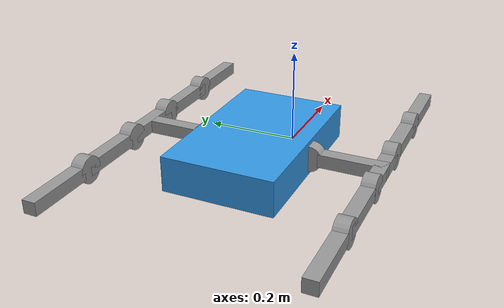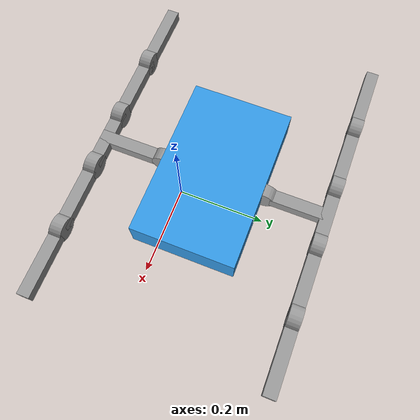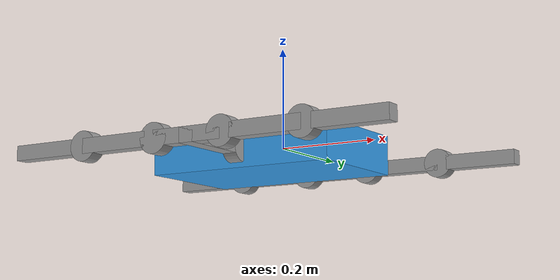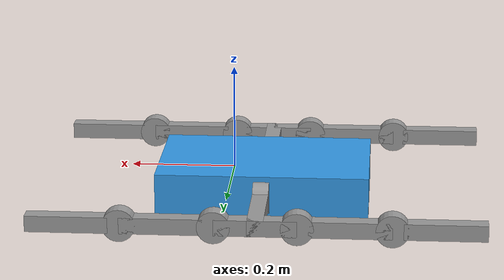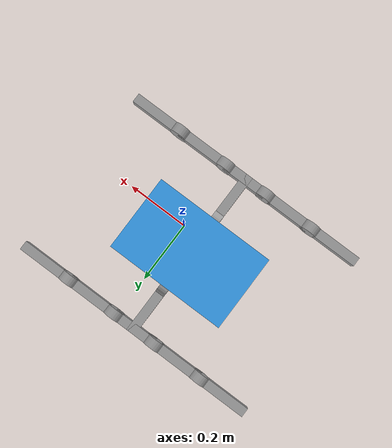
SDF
<?xml version='1.0'?>
<sdf version='1.6'>
  <model name='MS_Faraday_d'>
    <link name='CORE'>
      <pose frame=''>-0.063859 0.057301 -0 0 -0 0</pose>
      <inertial>
        <mass>1</mass>
        <inertia>
          <ixx>0.166667</ixx>
          <ixy>0</ixy>
          <ixz>0</ixz>
          <iyy>0.166667</iyy>
          <iyz>0</iyz>
          <izz>0.166667</izz>
        </inertia>
        <pose frame=''>0 0 0 0 -0 0</pose>
      </inertial>
      <self_collide>1</self_collide>
      <kinematic>0</kinematic>
      <gravity>1</gravity>
      <visual name='visual'>
        <pose frame=''>0 0 0 0 -0 0</pose>
        <geometry>
          <box>
            <size>0.4 0.25 0.08</size>
          </box>
        </geometry>
        <material>
          <lighting>1</lighting>
          <script>
            <uri>file://media/materials/scripts/gazebo.material</uri>
            <name>Gazebo/Grey</name>
          </script>
          <ambient>0.2 0.6 0.9 1</ambient>
          <diffuse>0.7 0.7 0.7 1</diffuse>
          <specular>0.01 0.01 0.01 1</specular>
          <emissive>0 0 0 1</emissive>
          <shader type='vertex'>
            <normal_map>__default__</normal_map>
          </shader>
        </material>
        <cast_shadows>1</cast_shadows>
        <transparency>0</transparency>
      </visual>
      <collision name='collision'>
        <laser_retro>0</laser_retro>
        <max_contacts>10</max_contacts>
        <pose frame=''>0 0 0 0 -0 0</pose>
        <geometry>
          <box>
            <size>0.4 0.25 0.08</size>
          </box>
        </geometry>
        <surface>
          <friction>
            <ode>
              <mu>1</mu>
              <mu2>1</mu2>
              <fdir1>0 0 0</fdir1>
              <slip1>0</slip1>
              <slip2>0</slip2>
            </ode>
            <torsional>
              <coefficient>1</coefficient>
              <patch_radius>0</patch_radius>
              <surface_radius>0</surface_radius>
              <use_patch_radius>1</use_patch_radius>
              <ode>
                <slip>0</slip>
              </ode>
            </torsional>
          </friction>
          <bounce>
            <restitution_coefficient>0</restitution_coefficient>
            <threshold>1e+06</threshold>
          </bounce>
          <contact>
            <collide_without_contact>0</collide_without_contact>
            <collide_without_contact_bitmask>1</collide_without_contact_bitmask>
            <collide_bitmask>1</collide_bitmask>
            <ode>
              <soft_cfm>0</soft_cfm>
              <soft_erp>0.2</soft_erp>
              <kp>1e+13</kp>
              <kd>1</kd>
              <max_vel>0.01</max_vel>
              <min_depth>0</min_depth>
            </ode>
            <bullet>
              <split_impulse>1</split_impulse>
              <split_impulse_penetration_threshold>-0.01</split_impulse_penetration_threshold>
              <soft_cfm>0</soft_cfm>
              <soft_erp>0.2</soft_erp>
              <kp>1e+13</kp>
              <kd>1</kd>
            </bullet>
          </contact>
        </surface>
      </collision>
    </link>
    <link name='L1'>
      <pose frame=''>-0.403859 -0.222699 0 4e-06 -6e-06 0</pose>
      <inertial>
        <mass>1</mass>
        <inertia>
          <ixx>0.166667</ixx>
          <ixy>0</ixy>
          <ixz>0</ixz>
          <iyy>0.166667</iyy>
          <iyz>0</iyz>
          <izz>0.166667</izz>
        </inertia>
        <pose frame=''>0 0 0 0 -0 0</pose>
      </inertial>
      <self_collide>1</self_collide>
      <kinematic>0</kinematic>
      <gravity>1</gravity>
      <visual name='visual'>
        <pose frame=''>0 0 0 0 -0 0</pose>
        <geometry>
          <box>
            <size>0.15 0.03 0.03</size>
          </box>
        </geometry>
        <material>
          <lighting>1</lighting>
          <script>
            <uri>file://media/materials/scripts/gazebo.material</uri>
            <name>Gazebo/Grey</name>
          </script>
          <ambient>1 1 1 1</ambient>
          <diffuse>0.7 0.7 0.7 1</diffuse>
          <specular>0.01 0.01 0.01 1</specular>
          <emissive>0 0 0 1</emissive>
          <shader type='vertex'>
            <normal_map>__default__</normal_map>
          </shader>
        </material>
        <cast_shadows>1</cast_shadows>
        <transparency>0</transparency>
      </visual>
      <collision name='collision'>
        <laser_retro>0</laser_retro>
        <max_contacts>10</max_contacts>
        <pose frame=''>0 0 0 0 -0 0</pose>
        <geometry>
          <box>
            <size>0.15 0.03 0.03</size>
          </box>
        </geometry>
        <surface>
          <friction>
            <ode>
              <mu>1</mu>
              <mu2>1</mu2>
              <fdir1>0 0 0</fdir1>
              <slip1>0</slip1>
              <slip2>0</slip2>
            </ode>
            <torsional>
              <coefficient>1</coefficient>
              <patch_radius>0</patch_radius>
              <surface_radius>0</surface_radius>
              <use_patch_radius>1</use_patch_radius>
              <ode>
                <slip>0</slip>
              </ode>
            </torsional>
          </friction>
          <bounce>
            <restitution_coefficient>0</restitution_coefficient>
            <threshold>1e+06</threshold>
          </bounce>
          <contact>
            <collide_without_contact>0</collide_without_contact>
            <collide_without_contact_bitmask>1</collide_without_contact_bitmask>
            <collide_bitmask>1</collide_bitmask>
            <ode>
              <soft_cfm>0</soft_cfm>
              <soft_erp>0.2</soft_erp>
              <kp>1e+13</kp>
              <kd>1</kd>
              <max_vel>0.01</max_vel>
              <min_depth>0</min_depth>
            </ode>
            <bullet>
              <split_impulse>1</split_impulse>
              <split_impulse_penetration_threshold>-0.01</split_impulse_penetration_threshold>
              <soft_cfm>0</soft_cfm>
              <soft_erp>0.2</soft_erp>
              <kp>1e+13</kp>
              <kd>1</kd>
            </bullet>
          </contact>
        </surface>
      </collision>
    </link>
    <link name='L2'>
      <pose frame=''>-0.233859 -0.222699 0 4e-06 -6e-06 0</pose>
      <inertial>
        <mass>1</mass>
        <inertia>
          <ixx>0.166667</ixx>
          <ixy>0</ixy>
          <ixz>0</ixz>
          <iyy>0.166667</iyy>
          <iyz>0</iyz>
          <izz>0.166667</izz>
        </inertia>
        <pose frame=''>0 0 0 0 -0 0</pose>
      </inertial>
      <self_collide>1</self_collide>
      <kinematic>0</kinematic>
      <gravity>1</gravity>
      <visual name='visual'>
        <pose frame=''>0 0 0 0 -0 0</pose>
        <geometry>
          <box>
            <size>0.15 0.03 0.03</size>
          </box>
        </geometry>
        <material>
          <lighting>1</lighting>
          <script>
            <uri>file://media/materials/scripts/gazebo.material</uri>
            <name>Gazebo/Grey</name>
          </script>
          <ambient>1 1 1 1</ambient>
          <diffuse>0.7 0.7 0.7 1</diffuse>
          <specular>0.01 0.01 0.01 1</specular>
          <emissive>0 0 0 1</emissive>
          <shader type='vertex'>
            <normal_map>__default__</normal_map>
          </shader>
        </material>
        <cast_shadows>1</cast_shadows>
        <transparency>0</transparency>
      </visual>
      <collision name='collision'>
        <laser_retro>0</laser_retro>
        <max_contacts>10</max_contacts>
        <pose frame=''>0 0 0 0 -0 0</pose>
        <geometry>
          <box>
            <size>0.15 0.03 0.03</size>
          </box>
        </geometry>
        <surface>
          <friction>
            <ode>
              <mu>1</mu>
              <mu2>1</mu2>
              <fdir1>0 0 0</fdir1>
              <slip1>0</slip1>
              <slip2>0</slip2>
            </ode>
            <torsional>
              <coefficient>1</coefficient>
              <patch_radius>0</patch_radius>
              <surface_radius>0</surface_radius>
              <use_patch_radius>1</use_patch_radius>
              <ode>
                <slip>0</slip>
              </ode>
            </torsional>
          </friction>
          <bounce>
            <restitution_coefficient>0</restitution_coefficient>
            <threshold>1e+06</threshold>
          </bounce>
          <contact>
            <collide_without_contact>0</collide_without_contact>
            <collide_without_contact_bitmask>1</collide_without_contact_bitmask>
            <collide_bitmask>1</collide_bitmask>
            <ode>
              <soft_cfm>0</soft_cfm>
              <soft_erp>0.2</soft_erp>
              <kp>1e+13</kp>
              <kd>1</kd>
              <max_vel>0.01</max_vel>
              <min_depth>0</min_depth>
            </ode>
            <bullet>
              <split_impulse>1</split_impulse>
              <split_impulse_penetration_threshold>-0.01</split_impulse_penetration_threshold>
              <soft_cfm>0</soft_cfm>
              <soft_erp>0.2</soft_erp>
              <kp>1e+13</kp>
              <kd>1</kd>
            </bullet>
          </contact>
        </surface>
      </collision>
    </link>
    <link name='L3-1'>
      <pose frame=''>-0.063859 -0.222699 -0 0 -6e-06 0</pose>
      <inertial>
        <mass>1</mass>
        <inertia>
          <ixx>0.166667</ixx>
          <ixy>0</ixy>
          <ixz>0</ixz>
          <iyy>0.166667</iyy>
          <iyz>0</iyz>
          <izz>0.166667</izz>
        </inertia>
        <pose frame=''>0 0 0 0 -0 0</pose>
      </inertial>
      <self_collide>1</self_collide>
      <kinematic>0</kinematic>
      <gravity>1</gravity>
      <visual name='visual'>
        <pose frame=''>0 0 0 0 -0 0</pose>
        <geometry>
          <box>
            <size>0.15 0.03 0.03</size>
          </box>
        </geometry>
        <material>
          <lighting>1</lighting>
          <script>
            <uri>file://media/materials/scripts/gazebo.material</uri>
            <name>Gazebo/Grey</name>
          </script>
          <ambient>1 1 1 1</ambient>
          <diffuse>0.7 0.7 0.7 1</diffuse>
          <specular>0.01 0.01 0.01 1</specular>
          <emissive>0 0 0 1</emissive>
          <shader type='vertex'>
            <normal_map>__default__</normal_map>
          </shader>
        </material>
        <cast_shadows>1</cast_shadows>
        <transparency>0</transparency>
      </visual>
      <collision name='collision'>
        <laser_retro>0</laser_retro>
        <max_contacts>10</max_contacts>
        <pose frame=''>0 0 0 0 -0 0</pose>
        <geometry>
          <box>
            <size>0.15 0.03 0.03</size>
          </box>
        </geometry>
        <surface>
          <friction>
            <ode>
              <mu>1</mu>
              <mu2>1</mu2>
              <fdir1>0 0 0</fdir1>
              <slip1>0</slip1>
              <slip2>0</slip2>
            </ode>
            <torsional>
              <coefficient>1</coefficient>
              <patch_radius>0</patch_radius>
              <surface_radius>0</surface_radius>
              <use_patch_radius>1</use_patch_radius>
              <ode>
                <slip>0</slip>
              </ode>
            </torsional>
          </friction>
          <bounce>
            <restitution_coefficient>0</restitution_coefficient>
            <threshold>1e+06</threshold>
          </bounce>
          <contact>
            <collide_without_contact>0</collide_without_contact>
            <collide_without_contact_bitmask>1</collide_without_contact_bitmask>
            <collide_bitmask>1</collide_bitmask>
            <ode>
              <soft_cfm>0</soft_cfm>
              <soft_erp>0.2</soft_erp>
              <kp>1e+13</kp>
              <kd>1</kd>
              <max_vel>0.01</max_vel>
              <min_depth>0</min_depth>
            </ode>
            <bullet>
              <split_impulse>1</split_impulse>
              <split_impulse_penetration_threshold>-0.01</split_impulse_penetration_threshold>
              <soft_cfm>0</soft_cfm>
              <soft_erp>0.2</soft_erp>
              <kp>1e+13</kp>
              <kd>1</kd>
            </bullet>
          </contact>
        </surface>
      </collision>
    </link>
    <link name='L3-2'>
      <pose frame=''>-0.063859 -0.162699 -0 -6e-06 -0 1.5708</pose>
      <inertial>
        <mass>1</mass>
        <inertia>
          <ixx>0.166667</ixx>
          <ixy>0</ixy>
          <ixz>0</ixz>
          <iyy>0.166667</iyy>
          <iyz>0</iyz>
          <izz>0.166667</izz>
        </inertia>
        <pose frame=''>0 0 0 0 -0 0</pose>
      </inertial>
      <self_collide>1</self_collide>
      <kinematic>0</kinematic>
      <gravity>1</gravity>
      <visual name='visual'>
        <pose frame=''>0 0 0 0 -0 0</pose>
        <geometry>
          <box>
            <size>0.15 0.03 0.03</size>
          </box>
        </geometry>
        <material>
          <lighting>1</lighting>
          <script>
            <uri>file://media/materials/scripts/gazebo.material</uri>
            <name>Gazebo/Grey</name>
          </script>
          <ambient>1 1 1 1</ambient>
          <diffuse>0.7 0.7 0.7 1</diffuse>
          <specular>0.01 0.01 0.01 1</specular>
          <emissive>0 0 0 1</emissive>
          <shader type='vertex'>
            <normal_map>__default__</normal_map>
          </shader>
        </material>
        <cast_shadows>1</cast_shadows>
        <transparency>0</transparency>
      </visual>
      <collision name='collision'>
        <laser_retro>0</laser_retro>
        <max_contacts>10</max_contacts>
        <pose frame=''>0 0 0 0 -0 0</pose>
        <geometry>
          <box>
            <size>0.15 0.03 0.03</size>
          </box>
        </geometry>
        <surface>
          <friction>
            <ode>
              <mu>1</mu>
              <mu2>1</mu2>
              <fdir1>0 0 0</fdir1>
              <slip1>0</slip1>
              <slip2>0</slip2>
            </ode>
            <torsional>
              <coefficient>1</coefficient>
              <patch_radius>0</patch_radius>
              <surface_radius>0</surface_radius>
              <use_patch_radius>1</use_patch_radius>
              <ode>
                <slip>0</slip>
              </ode>
            </torsional>
          </friction>
          <bounce>
            <restitution_coefficient>0</restitution_coefficient>
            <threshold>1e+06</threshold>
          </bounce>
          <contact>
            <collide_without_contact>0</collide_without_contact>
            <collide_without_contact_bitmask>1</collide_without_contact_bitmask>
            <collide_bitmask>1</collide_bitmask>
            <ode>
              <soft_cfm>0</soft_cfm>
              <soft_erp>0.2</soft_erp>
              <kp>1e+13</kp>
              <kd>1</kd>
              <max_vel>0.01</max_vel>
              <min_depth>0</min_depth>
            </ode>
            <bullet>
              <split_impulse>1</split_impulse>
              <split_impulse_penetration_threshold>-0.01</split_impulse_penetration_threshold>
              <soft_cfm>0</soft_cfm>
              <soft_erp>0.2</soft_erp>
              <kp>1e+13</kp>
              <kd>1</kd>
            </bullet>
          </contact>
        </surface>
      </collision>
    </link>
    <link name='L4'>
      <pose frame=''>0.106141 -0.222699 1e-06 1e-06 -6e-06 0</pose>
      <inertial>
        <mass>1</mass>
        <inertia>
          <ixx>0.166667</ixx>
          <ixy>0</ixy>
          <ixz>0</ixz>
          <iyy>0.166667</iyy>
          <iyz>0</iyz>
          <izz>0.166667</izz>
        </inertia>
        <pose frame=''>0 0 0 0 -0 0</pose>
      </inertial>
      <self_collide>1</self_collide>
      <kinematic>0</kinematic>
      <gravity>1</gravity>
      <visual name='visual'>
        <pose frame=''>0 0 0 0 -0 0</pose>
        <geometry>
          <box>
            <size>0.15 0.03 0.03</size>
          </box>
        </geometry>
        <material>
          <lighting>1</lighting>
          <script>
            <uri>file://media/materials/scripts/gazebo.material</uri>
            <name>Gazebo/Grey</name>
          </script>
          <ambient>1 1 1 1</ambient>
          <diffuse>0.7 0.7 0.7 1</diffuse>
          <specular>0.01 0.01 0.01 1</specular>
          <emissive>0 0 0 1</emissive>
          <shader type='vertex'>
            <normal_map>__default__</normal_map>
          </shader>
        </material>
        <cast_shadows>1</cast_shadows>
        <transparency>0</transparency>
      </visual>
      <collision name='collision'>
        <laser_retro>0</laser_retro>
        <max_contacts>10</max_contacts>
        <pose frame=''>0 0 0 0 -0 0</pose>
        <geometry>
          <box>
            <size>0.15 0.03 0.03</size>
          </box>
        </geometry>
        <surface>
          <friction>
            <ode>
              <mu>1</mu>
              <mu2>1</mu2>
              <fdir1>0 0 0</fdir1>
              <slip1>0</slip1>
              <slip2>0</slip2>
            </ode>
            <torsional>
              <coefficient>1</coefficient>
              <patch_radius>0</patch_radius>
              <surface_radius>0</surface_radius>
              <use_patch_radius>1</use_patch_radius>
              <ode>
                <slip>0</slip>
              </ode>
            </torsional>
          </friction>
          <bounce>
            <restitution_coefficient>0</restitution_coefficient>
            <threshold>1e+06</threshold>
          </bounce>
          <contact>
            <collide_without_contact>0</collide_without_contact>
            <collide_without_contact_bitmask>1</collide_without_contact_bitmask>
            <collide_bitmask>1</collide_bitmask>
            <ode>
              <soft_cfm>0</soft_cfm>
              <soft_erp>0.2</soft_erp>
              <kp>1e+13</kp>
              <kd>1</kd>
              <max_vel>0.01</max_vel>
              <min_depth>0</min_depth>
            </ode>
            <bullet>
              <split_impulse>1</split_impulse>
              <split_impulse_penetration_threshold>-0.01</split_impulse_penetration_threshold>
              <soft_cfm>0</soft_cfm>
              <soft_erp>0.2</soft_erp>
              <kp>1e+13</kp>
              <kd>1</kd>
            </bullet>
          </contact>
        </surface>
      </collision>
    </link>
    <link name='L5'>
      <pose frame=''>0.276141 -0.222699 2e-06 4e-06 -6e-06 0</pose>
      <inertial>
        <mass>1</mass>
        <inertia>
          <ixx>0.166667</ixx>
          <ixy>0</ixy>
          <ixz>0</ixz>
          <iyy>0.166667</iyy>
          <iyz>0</iyz>
          <izz>0.166667</izz>
        </inertia>
        <pose frame=''>0 0 0 0 -0 0</pose>
      </inertial>
      <self_collide>1</self_collide>
      <kinematic>0</kinematic>
      <gravity>1</gravity>
      <visual name='visual'>
        <pose frame=''>0 0 0 0 -0 0</pose>
        <geometry>
          <box>
            <size>0.15 0.03 0.03</size>
          </box>
        </geometry>
        <material>
          <lighting>1</lighting>
          <script>
            <uri>file://media/materials/scripts/gazebo.material</uri>
            <name>Gazebo/Grey</name>
          </script>
          <ambient>1 1 1 1</ambient>
          <diffuse>0.7 0.7 0.7 1</diffuse>
          <specular>0.01 0.01 0.01 1</specular>
          <emissive>0 0 0 1</emissive>
          <shader type='vertex'>
            <normal_map>__default__</normal_map>
          </shader>
        </material>
        <cast_shadows>1</cast_shadows>
        <transparency>0</transparency>
      </visual>
      <collision name='__default__'>
        <laser_retro>0</laser_retro>
        <max_contacts>10</max_contacts>
        <pose frame=''>0 0 0 0 -0 0</pose>
        <geometry>
          <box>
            <size>0.15 0.03 0.03</size>
          </box>
        </geometry>
        <surface>
          <friction>
            <ode>
              <mu>1</mu>
              <mu2>1</mu2>
              <fdir1>0 0 0</fdir1>
              <slip1>0</slip1>
              <slip2>0</slip2>
            </ode>
            <torsional>
              <coefficient>1</coefficient>
              <patch_radius>0</patch_radius>
              <surface_radius>0</surface_radius>
              <use_patch_radius>1</use_patch_radius>
              <ode>
                <slip>0</slip>
              </ode>
            </torsional>
          </friction>
          <bounce>
            <restitution_coefficient>0</restitution_coefficient>
            <threshold>1e+06</threshold>
          </bounce>
          <contact>
            <collide_without_contact>0</collide_without_contact>
            <collide_without_contact_bitmask>1</collide_without_contact_bitmask>
            <collide_bitmask>1</collide_bitmask>
            <ode>
              <soft_cfm>0</soft_cfm>
              <soft_erp>0.2</soft_erp>
              <kp>1e+13</kp>
              <kd>1</kd>
              <max_vel>0.01</max_vel>
              <min_depth>0</min_depth>
            </ode>
            <bullet>
              <split_impulse>1</split_impulse>
              <split_impulse_penetration_threshold>-0.01</split_impulse_penetration_threshold>
              <soft_cfm>0</soft_cfm>
              <soft_erp>0.2</soft_erp>
              <kp>1e+13</kp>
              <kd>1</kd>
            </bullet>
          </contact>
        </surface>
      </collision>
      <collision name='collision'>
        <laser_retro>0</laser_retro>
        <max_contacts>10</max_contacts>
        <pose frame=''>0 0 0 0 -0 0</pose>
        <geometry>
          <box>
            <size>0.15 0.03 0.03</size>
          </box>
        </geometry>
        <surface>
          <friction>
            <ode>
              <mu>1</mu>
              <mu2>1</mu2>
              <fdir1>0 0 0</fdir1>
              <slip1>0</slip1>
              <slip2>0</slip2>
            </ode>
            <torsional>
              <coefficient>1</coefficient>
              <patch_radius>0</patch_radius>
              <surface_radius>0</surface_radius>
              <use_patch_radius>1</use_patch_radius>
              <ode>
                <slip>0</slip>
              </ode>
            </torsional>
          </friction>
          <bounce>
            <restitution_coefficient>0</restitution_coefficient>
            <threshold>1e+06</threshold>
          </bounce>
          <contact>
            <collide_without_contact>0</collide_without_contact>
            <collide_without_contact_bitmask>1</collide_without_contact_bitmask>
            <collide_bitmask>1</collide_bitmask>
            <ode>
              <soft_cfm>0</soft_cfm>
              <soft_erp>0.2</soft_erp>
              <kp>1e+13</kp>
              <kd>1</kd>
              <max_vel>0.01</max_vel>
              <min_depth>0</min_depth>
            </ode>
            <bullet>
              <split_impulse>1</split_impulse>
              <split_impulse_penetration_threshold>-0.01</split_impulse_penetration_threshold>
              <soft_cfm>0</soft_cfm>
              <soft_erp>0.2</soft_erp>
              <kp>1e+13</kp>
              <kd>1</kd>
            </bullet>
          </contact>
        </surface>
      </collision>
    </link>
    <link name='ML-0'>
      <pose frame=''>-0.063859 -0.067699 0 -1e-05 1.57079 -1e-05</pose>
      <inertial>
        <mass>1</mass>
        <inertia>
          <ixx>0.145833</ixx>
          <ixy>0</ixy>
          <ixz>0</ixz>
          <iyy>0.145833</iyy>
          <iyz>0</iyz>
          <izz>0.125</izz>
        </inertia>
        <pose frame=''>0 0 0 0 -0 0</pose>
      </inertial>
      <self_collide>0</self_collide>
      <kinematic>0</kinematic>
      <gravity>1</gravity>
      <visual name='visual'>
        <pose frame=''>0 0 0 0 -0 0</pose>
        <geometry>
          <cylinder>
            <radius>0.03</radius>
            <length>0.03</length>
          </cylinder>
        </geometry>
        <material>
          <lighting>1</lighting>
          <script>
            <uri>file://media/materials/scripts/gazebo.material</uri>
            <name>Gazebo/Grey</name>
          </script>
          <ambient>0 0 0 1</ambient>
          <diffuse>0.7 0.7 0.7 1</diffuse>
          <specular>0.01 0.01 0.01 1</specular>
          <emissive>0 0 0 1</emissive>
          <shader type='vertex'>
            <normal_map>__default__</normal_map>
          </shader>
        </material>
        <cast_shadows>1</cast_shadows>
        <transparency>0</transparency>
      </visual>
      <collision name='collision'>
        <laser_retro>0</laser_retro>
        <max_contacts>10</max_contacts>
        <pose frame=''>0 0 0 0 -0 0</pose>
        <geometry>
          <cylinder>
            <radius>0.03</radius>
            <length>0.03</length>
          </cylinder>
        </geometry>
        <surface>
          <friction>
            <ode>
              <mu>1</mu>
              <mu2>1</mu2>
              <fdir1>0 0 0</fdir1>
              <slip1>0</slip1>
              <slip2>0</slip2>
            </ode>
            <torsional>
              <coefficient>1</coefficient>
              <patch_radius>0</patch_radius>
              <surface_radius>0</surface_radius>
              <use_patch_radius>1</use_patch_radius>
              <ode>
                <slip>0</slip>
              </ode>
            </torsional>
          </friction>
          <bounce>
            <restitution_coefficient>0</restitution_coefficient>
            <threshold>1e+06</threshold>
          </bounce>
          <contact>
            <collide_without_contact>0</collide_without_contact>
            <collide_without_contact_bitmask>1</collide_without_contact_bitmask>
            <collide_bitmask>1</collide_bitmask>
            <ode>
              <soft_cfm>0</soft_cfm>
              <soft_erp>0.2</soft_erp>
              <kp>1e+13</kp>
              <kd>1</kd>
              <max_vel>0.01</max_vel>
              <min_depth>0</min_depth>
            </ode>
            <bullet>
              <split_impulse>1</split_impulse>
              <split_impulse_penetration_threshold>-0.01</split_impulse_penetration_threshold>
              <soft_cfm>0</soft_cfm>
              <soft_erp>0.2</soft_erp>
              <kp>1e+13</kp>
              <kd>1</kd>
            </bullet>
          </contact>
        </surface>
      </collision>
    </link>
    <link name='ML-1'>
      <pose frame=''>-0.308859 -0.222699 0 1.5708 -6e-06 0</pose>
      <inertial>
        <mass>1</mass>
        <inertia>
          <ixx>0.145833</ixx>
          <ixy>0</ixy>
          <ixz>0</ixz>
          <iyy>0.145833</iyy>
          <iyz>0</iyz>
          <izz>0.125</izz>
        </inertia>
        <pose frame=''>0 0 0 0 -0 0</pose>
      </inertial>
      <self_collide>0</self_collide>
      <kinematic>0</kinematic>
      <gravity>1</gravity>
      <visual name='visual'>
        <pose frame=''>0 0 0 0 -0 0</pose>
        <geometry>
          <cylinder>
            <radius>0.03</radius>
            <length>0.03</length>
          </cylinder>
        </geometry>
        <material>
          <lighting>1</lighting>
          <script>
            <uri>file://media/materials/scripts/gazebo.material</uri>
            <name>Gazebo/Grey</name>
          </script>
          <ambient>0 0 0 1</ambient>
          <diffuse>0.7 0.7 0.7 1</diffuse>
          <specular>0.01 0.01 0.01 1</specular>
          <emissive>0 0 0 1</emissive>
          <shader type='vertex'>
            <normal_map>__default__</normal_map>
          </shader>
        </material>
        <cast_shadows>1</cast_shadows>
        <transparency>0</transparency>
      </visual>
      <collision name='collision'>
        <laser_retro>0</laser_retro>
        <max_contacts>10</max_contacts>
        <pose frame=''>0 0 0 0 -0 0</pose>
        <geometry>
          <cylinder>
            <radius>0.03</radius>
            <length>0.03</length>
          </cylinder>
        </geometry>
        <surface>
          <friction>
            <ode>
              <mu>1</mu>
              <mu2>1</mu2>
              <fdir1>0 0 0</fdir1>
              <slip1>0</slip1>
              <slip2>0</slip2>
            </ode>
            <torsional>
              <coefficient>1</coefficient>
              <patch_radius>0</patch_radius>
              <surface_radius>0</surface_radius>
              <use_patch_radius>1</use_patch_radius>
              <ode>
                <slip>0</slip>
              </ode>
            </torsional>
          </friction>
          <bounce>
            <restitution_coefficient>0</restitution_coefficient>
            <threshold>1e+06</threshold>
          </bounce>
          <contact>
            <collide_without_contact>0</collide_without_contact>
            <collide_without_contact_bitmask>1</collide_without_contact_bitmask>
            <collide_bitmask>1</collide_bitmask>
            <ode>
              <soft_cfm>0</soft_cfm>
              <soft_erp>0.2</soft_erp>
              <kp>1e+13</kp>
              <kd>1</kd>
              <max_vel>0.01</max_vel>
              <min_depth>0</min_depth>
            </ode>
            <bullet>
              <split_impulse>1</split_impulse>
              <split_impulse_penetration_threshold>-0.01</split_impulse_penetration_threshold>
              <soft_cfm>0</soft_cfm>
              <soft_erp>0.2</soft_erp>
              <kp>1e+13</kp>
              <kd>1</kd>
            </bullet>
          </contact>
        </surface>
      </collision>
    </link>
    <link name='ML-2'>
      <pose frame=''>-0.138859 -0.222699 0 1.5708 -6e-06 0</pose>
      <inertial>
        <mass>1</mass>
        <inertia>
          <ixx>0.145833</ixx>
          <ixy>0</ixy>
          <ixz>0</ixz>
          <iyy>0.145833</iyy>
          <iyz>0</iyz>
          <izz>0.125</izz>
        </inertia>
        <pose frame=''>0 0 0 0 -0 0</pose>
      </inertial>
      <self_collide>0</self_collide>
      <kinematic>0</kinematic>
      <gravity>1</gravity>
      <visual name='visual'>
        <pose frame=''>0 0 0 0 -0 0</pose>
        <geometry>
          <cylinder>
            <radius>0.03</radius>
            <length>0.03</length>
          </cylinder>
        </geometry>
        <material>
          <lighting>1</lighting>
          <script>
            <uri>file://media/materials/scripts/gazebo.material</uri>
            <name>Gazebo/Grey</name>
          </script>
          <ambient>0 0 0 1</ambient>
          <diffuse>0.7 0.7 0.7 1</diffuse>
          <specular>0.01 0.01 0.01 1</specular>
          <emissive>0 0 0 1</emissive>
          <shader type='vertex'>
            <normal_map>__default__</normal_map>
          </shader>
        </material>
        <cast_shadows>1</cast_shadows>
        <transparency>0</transparency>
      </visual>
      <collision name='collision'>
        <laser_retro>0</laser_retro>
        <max_contacts>10</max_contacts>
        <pose frame=''>0 0 0 0 -0 0</pose>
        <geometry>
          <cylinder>
            <radius>0.03</radius>
            <length>0.03</length>
          </cylinder>
        </geometry>
        <surface>
          <friction>
            <ode>
              <mu>1</mu>
              <mu2>1</mu2>
              <fdir1>0 0 0</fdir1>
              <slip1>0</slip1>
              <slip2>0</slip2>
            </ode>
            <torsional>
              <coefficient>1</coefficient>
              <patch_radius>0</patch_radius>
              <surface_radius>0</surface_radius>
              <use_patch_radius>1</use_patch_radius>
              <ode>
                <slip>0</slip>
              </ode>
            </torsional>
          </friction>
          <bounce>
            <restitution_coefficient>0</restitution_coefficient>
            <threshold>1e+06</threshold>
          </bounce>
          <contact>
            <collide_without_contact>0</collide_without_contact>
            <collide_without_contact_bitmask>1</collide_without_contact_bitmask>
            <collide_bitmask>1</collide_bitmask>
            <ode>
              <soft_cfm>0</soft_cfm>
              <soft_erp>0.2</soft_erp>
              <kp>1e+13</kp>
              <kd>1</kd>
              <max_vel>0.01</max_vel>
              <min_depth>0</min_depth>
            </ode>
            <bullet>
              <split_impulse>1</split_impulse>
              <split_impulse_penetration_threshold>-0.01</split_impulse_penetration_threshold>
              <soft_cfm>0</soft_cfm>
              <soft_erp>0.2</soft_erp>
              <kp>1e+13</kp>
              <kd>1</kd>
            </bullet>
          </contact>
        </surface>
      </collision>
    </link>
    <link name='ML-3'>
      <pose frame=''>0.011141 -0.222699 -0 1.5708 -6e-06 0</pose>
      <inertial>
        <mass>1</mass>
        <inertia>
          <ixx>0.145833</ixx>
          <ixy>0</ixy>
          <ixz>0</ixz>
          <iyy>0.145833</iyy>
          <iyz>0</iyz>
          <izz>0.125</izz>
        </inertia>
        <pose frame=''>0 0 0 0 -0 0</pose>
      </inertial>
      <self_collide>0</self_collide>
      <kinematic>0</kinematic>
      <gravity>1</gravity>
      <visual name='visual'>
        <pose frame=''>0 0 0 0 -0 0</pose>
        <geometry>
          <cylinder>
            <radius>0.03</radius>
            <length>0.03</length>
          </cylinder>
        </geometry>
        <material>
          <lighting>1</lighting>
          <script>
            <uri>file://media/materials/scripts/gazebo.material</uri>
            <name>Gazebo/Grey</name>
          </script>
          <ambient>0 0 0 1</ambient>
          <diffuse>0.7 0.7 0.7 1</diffuse>
          <specular>0.01 0.01 0.01 1</specular>
          <emissive>0 0 0 1</emissive>
          <shader type='vertex'>
            <normal_map>__default__</normal_map>
          </shader>
        </material>
        <cast_shadows>1</cast_shadows>
        <transparency>0</transparency>
      </visual>
      <collision name='collision'>
        <laser_retro>0</laser_retro>
        <max_contacts>10</max_contacts>
        <pose frame=''>0 0 0 0 -0 0</pose>
        <geometry>
          <cylinder>
            <radius>0.03</radius>
            <length>0.03</length>
          </cylinder>
        </geometry>
        <surface>
          <friction>
            <ode>
              <mu>1</mu>
              <mu2>1</mu2>
              <fdir1>0 0 0</fdir1>
              <slip1>0</slip1>
              <slip2>0</slip2>
            </ode>
            <torsional>
              <coefficient>1</coefficient>
              <patch_radius>0</patch_radius>
              <surface_radius>0</surface_radius>
              <use_patch_radius>1</use_patch_radius>
              <ode>
                <slip>0</slip>
              </ode>
            </torsional>
          </friction>
          <bounce>
            <restitution_coefficient>0</restitution_coefficient>
            <threshold>1e+06</threshold>
          </bounce>
          <contact>
            <collide_without_contact>0</collide_without_contact>
            <collide_without_contact_bitmask>1</collide_without_contact_bitmask>
            <collide_bitmask>1</collide_bitmask>
            <ode>
              <soft_cfm>0</soft_cfm>
              <soft_erp>0.2</soft_erp>
              <kp>1e+13</kp>
              <kd>1</kd>
              <max_vel>0.01</max_vel>
              <min_depth>0</min_depth>
            </ode>
            <bullet>
              <split_impulse>1</split_impulse>
              <split_impulse_penetration_threshold>-0.01</split_impulse_penetration_threshold>
              <soft_cfm>0</soft_cfm>
              <soft_erp>0.2</soft_erp>
              <kp>1e+13</kp>
              <kd>1</kd>
            </bullet>
          </contact>
        </surface>
      </collision>
    </link>
    <link name='ML-4'>
      <pose frame=''>0.181141 -0.222699 1e-06 1.5708 -6e-06 0</pose>
      <inertial>
        <mass>1</mass>
        <inertia>
          <ixx>0.145833</ixx>
          <ixy>0</ixy>
          <ixz>0</ixz>
          <iyy>0.145833</iyy>
          <iyz>0</iyz>
          <izz>0.125</izz>
        </inertia>
        <pose frame=''>0 0 0 0 -0 0</pose>
      </inertial>
      <self_collide>0</self_collide>
      <kinematic>0</kinematic>
      <gravity>1</gravity>
      <visual name='visual_0'>
        <pose frame=''>0 0 0 0 -0 0</pose>
        <geometry>
          <cylinder>
            <radius>0.03</radius>
            <length>0.03</length>
          </cylinder>
        </geometry>
        <material>
          <lighting>1</lighting>
          <script>
            <uri>file://media/materials/scripts/gazebo.material</uri>
            <name>Gazebo/Grey</name>
          </script>
          <ambient>0 0 0 1</ambient>
          <diffuse>0.7 0.7 0.7 1</diffuse>
          <specular>0.01 0.01 0.01 1</specular>
          <emissive>0 0 0 1</emissive>
          <shader type='vertex'>
            <normal_map>__default__</normal_map>
          </shader>
        </material>
        <cast_shadows>1</cast_shadows>
        <transparency>0</transparency>
      </visual>
      <collision name='collision'>
        <laser_retro>0</laser_retro>
        <max_contacts>10</max_contacts>
        <pose frame=''>0 0 0 0 -0 0</pose>
        <geometry>
          <cylinder>
            <radius>0.03</radius>
            <length>0.03</length>
          </cylinder>
        </geometry>
        <surface>
          <friction>
            <ode>
              <mu>1</mu>
              <mu2>1</mu2>
              <fdir1>0 0 0</fdir1>
              <slip1>0</slip1>
              <slip2>0</slip2>
            </ode>
            <torsional>
              <coefficient>1</coefficient>
              <patch_radius>0</patch_radius>
              <surface_radius>0</surface_radius>
              <use_patch_radius>1</use_patch_radius>
              <ode>
                <slip>0</slip>
              </ode>
            </torsional>
          </friction>
          <bounce>
            <restitution_coefficient>0</restitution_coefficient>
            <threshold>1e+06</threshold>
          </bounce>
          <contact>
            <collide_without_contact>0</collide_without_contact>
            <collide_without_contact_bitmask>1</collide_without_contact_bitmask>
            <collide_bitmask>1</collide_bitmask>
            <ode>
              <soft_cfm>0</soft_cfm>
              <soft_erp>0.2</soft_erp>
              <kp>1e+13</kp>
              <kd>1</kd>
              <max_vel>0.01</max_vel>
              <min_depth>0</min_depth>
            </ode>
            <bullet>
              <split_impulse>1</split_impulse>
              <split_impulse_penetration_threshold>-0.01</split_impulse_penetration_threshold>
              <soft_cfm>0</soft_cfm>
              <soft_erp>0.2</soft_erp>
              <kp>1e+13</kp>
              <kd>1</kd>
            </bullet>
          </contact>
        </surface>
      </collision>
    </link>
    <link name='MR-5'>
      <pose frame=''>-0.063859 0.182301 0 -1e-05 1.57079 -1e-05</pose>
      <inertial>
        <mass>1</mass>
        <inertia>
          <ixx>0.145833</ixx>
          <ixy>0</ixy>
          <ixz>0</ixz>
          <iyy>0.145833</iyy>
          <iyz>0</iyz>
          <izz>0.125</izz>
        </inertia>
        <pose frame=''>0 0 0 0 -0 0</pose>
      </inertial>
      <self_collide>0</self_collide>
      <kinematic>0</kinematic>
      <gravity>1</gravity>
      <visual name='visual'>
        <pose frame=''>0 0 0 0 -0 0</pose>
        <geometry>
          <cylinder>
            <radius>0.03</radius>
            <length>0.03</length>
          </cylinder>
        </geometry>
        <material>
          <lighting>1</lighting>
          <script>
            <uri>file://media/materials/scripts/gazebo.material</uri>
            <name>Gazebo/Grey</name>
          </script>
          <ambient>0 0 0 1</ambient>
          <diffuse>0.7 0.7 0.7 1</diffuse>
          <specular>0.01 0.01 0.01 1</specular>
          <emissive>0 0 0 1</emissive>
          <shader type='vertex'>
            <normal_map>__default__</normal_map>
          </shader>
        </material>
        <cast_shadows>1</cast_shadows>
        <transparency>0</transparency>
      </visual>
      <collision name='collision'>
        <laser_retro>0</laser_retro>
        <max_contacts>10</max_contacts>
        <pose frame=''>0 0 0 0 -0 0</pose>
        <geometry>
          <cylinder>
            <radius>0.03</radius>
            <length>0.03</length>
          </cylinder>
        </geometry>
        <surface>
          <friction>
            <ode>
              <mu>1</mu>
              <mu2>1</mu2>
              <fdir1>0 0 0</fdir1>
              <slip1>0</slip1>
              <slip2>0</slip2>
            </ode>
            <torsional>
              <coefficient>1</coefficient>
              <patch_radius>0</patch_radius>
              <surface_radius>0</surface_radius>
              <use_patch_radius>1</use_patch_radius>
              <ode>
                <slip>0</slip>
              </ode>
            </torsional>
          </friction>
          <bounce>
            <restitution_coefficient>0</restitution_coefficient>
            <threshold>1e+06</threshold>
          </bounce>
          <contact>
            <collide_without_contact>0</collide_without_contact>
            <collide_without_contact_bitmask>1</collide_without_contact_bitmask>
            <collide_bitmask>1</collide_bitmask>
            <ode>
              <soft_cfm>0</soft_cfm>
              <soft_erp>0.2</soft_erp>
              <kp>1e+13</kp>
              <kd>1</kd>
              <max_vel>0.01</max_vel>
              <min_depth>0</min_depth>
            </ode>
            <bullet>
              <split_impulse>1</split_impulse>
              <split_impulse_penetration_threshold>-0.01</split_impulse_penetration_threshold>
              <soft_cfm>0</soft_cfm>
              <soft_erp>0.2</soft_erp>
              <kp>1e+13</kp>
              <kd>1</kd>
            </bullet>
          </contact>
        </surface>
      </collision>
    </link>
    <link name='MR-6'>
      <pose frame=''>-0.308859 0.337301 -1e-06 1.5708 -6e-06 0</pose>
      <inertial>
        <mass>1</mass>
        <inertia>
          <ixx>0.145833</ixx>
          <ixy>0</ixy>
          <ixz>0</ixz>
          <iyy>0.145833</iyy>
          <iyz>0</iyz>
          <izz>0.125</izz>
        </inertia>
        <pose frame=''>0 0 0 0 -0 0</pose>
      </inertial>
      <self_collide>0</self_collide>
      <kinematic>0</kinematic>
      <gravity>1</gravity>
      <visual name='visual'>
        <pose frame=''>0 0 0 0 -0 0</pose>
        <geometry>
          <cylinder>
            <radius>0.03</radius>
            <length>0.03</length>
          </cylinder>
        </geometry>
        <material>
          <lighting>1</lighting>
          <script>
            <uri>file://media/materials/scripts/gazebo.material</uri>
            <name>Gazebo/Grey</name>
          </script>
          <ambient>0 0 0 1</ambient>
          <diffuse>0.7 0.7 0.7 1</diffuse>
          <specular>0.01 0.01 0.01 1</specular>
          <emissive>0 0 0 1</emissive>
          <shader type='vertex'>
            <normal_map>__default__</normal_map>
          </shader>
        </material>
        <cast_shadows>1</cast_shadows>
        <transparency>0</transparency>
      </visual>
      <collision name='collision'>
        <laser_retro>0</laser_retro>
        <max_contacts>10</max_contacts>
        <pose frame=''>0 0 0 0 -0 0</pose>
        <geometry>
          <cylinder>
            <radius>0.03</radius>
            <length>0.03</length>
          </cylinder>
        </geometry>
        <surface>
          <friction>
            <ode>
              <mu>1</mu>
              <mu2>1</mu2>
              <fdir1>0 0 0</fdir1>
              <slip1>0</slip1>
              <slip2>0</slip2>
            </ode>
            <torsional>
              <coefficient>1</coefficient>
              <patch_radius>0</patch_radius>
              <surface_radius>0</surface_radius>
              <use_patch_radius>1</use_patch_radius>
              <ode>
                <slip>0</slip>
              </ode>
            </torsional>
          </friction>
          <bounce>
            <restitution_coefficient>0</restitution_coefficient>
            <threshold>1e+06</threshold>
          </bounce>
          <contact>
            <collide_without_contact>0</collide_without_contact>
            <collide_without_contact_bitmask>1</collide_without_contact_bitmask>
            <collide_bitmask>1</collide_bitmask>
            <ode>
              <soft_cfm>0</soft_cfm>
              <soft_erp>0.2</soft_erp>
              <kp>1e+13</kp>
              <kd>1</kd>
              <max_vel>0.01</max_vel>
              <min_depth>0</min_depth>
            </ode>
            <bullet>
              <split_impulse>1</split_impulse>
              <split_impulse_penetration_threshold>-0.01</split_impulse_penetration_threshold>
              <soft_cfm>0</soft_cfm>
              <soft_erp>0.2</soft_erp>
              <kp>1e+13</kp>
              <kd>1</kd>
            </bullet>
          </contact>
        </surface>
      </collision>
    </link>
    <link name='MR-7'>
      <pose frame=''>-0.138859 0.337301 -0 1.5708 -6e-06 0</pose>
      <inertial>
        <mass>1</mass>
        <inertia>
          <ixx>0.145833</ixx>
          <ixy>0</ixy>
          <ixz>0</ixz>
          <iyy>0.145833</iyy>
          <iyz>0</iyz>
          <izz>0.125</izz>
        </inertia>
        <pose frame=''>0 0 0 0 -0 0</pose>
      </inertial>
      <self_collide>0</self_collide>
      <kinematic>0</kinematic>
      <gravity>1</gravity>
      <visual name='visual'>
        <pose frame=''>0 0 0 0 -0 0</pose>
        <geometry>
          <cylinder>
            <radius>0.03</radius>
            <length>0.03</length>
          </cylinder>
        </geometry>
        <material>
          <lighting>1</lighting>
          <script>
            <uri>file://media/materials/scripts/gazebo.material</uri>
            <name>Gazebo/Grey</name>
          </script>
          <ambient>0 0 0 1</ambient>
          <diffuse>0.7 0.7 0.7 1</diffuse>
          <specular>0.01 0.01 0.01 1</specular>
          <emissive>0 0 0 1</emissive>
          <shader type='vertex'>
            <normal_map>__default__</normal_map>
          </shader>
        </material>
        <cast_shadows>1</cast_shadows>
        <transparency>0</transparency>
      </visual>
      <collision name='collision'>
        <laser_retro>0</laser_retro>
        <max_contacts>10</max_contacts>
        <pose frame=''>0 0 0 0 -0 0</pose>
        <geometry>
          <cylinder>
            <radius>0.03</radius>
            <length>0.03</length>
          </cylinder>
        </geometry>
        <surface>
          <friction>
            <ode>
              <mu>1</mu>
              <mu2>1</mu2>
              <fdir1>0 0 0</fdir1>
              <slip1>0</slip1>
              <slip2>0</slip2>
            </ode>
            <torsional>
              <coefficient>1</coefficient>
              <patch_radius>0</patch_radius>
              <surface_radius>0</surface_radius>
              <use_patch_radius>1</use_patch_radius>
              <ode>
                <slip>0</slip>
              </ode>
            </torsional>
          </friction>
          <bounce>
            <restitution_coefficient>0</restitution_coefficient>
            <threshold>1e+06</threshold>
          </bounce>
          <contact>
            <collide_without_contact>0</collide_without_contact>
            <collide_without_contact_bitmask>1</collide_without_contact_bitmask>
            <collide_bitmask>1</collide_bitmask>
            <ode>
              <soft_cfm>0</soft_cfm>
              <soft_erp>0.2</soft_erp>
              <kp>1e+13</kp>
              <kd>1</kd>
              <max_vel>0.01</max_vel>
              <min_depth>0</min_depth>
            </ode>
            <bullet>
              <split_impulse>1</split_impulse>
              <split_impulse_penetration_threshold>-0.01</split_impulse_penetration_threshold>
              <soft_cfm>0</soft_cfm>
              <soft_erp>0.2</soft_erp>
              <kp>1e+13</kp>
              <kd>1</kd>
            </bullet>
          </contact>
        </surface>
      </collision>
    </link>
    <link name='MR-8'>
      <pose frame=''>0.011141 0.337301 0 1.5708 -6e-06 0</pose>
      <inertial>
        <mass>1</mass>
        <inertia>
          <ixx>0.145833</ixx>
          <ixy>0</ixy>
          <ixz>0</ixz>
          <iyy>0.145833</iyy>
          <iyz>0</iyz>
          <izz>0.125</izz>
        </inertia>
        <pose frame=''>0 0 0 0 -0 0</pose>
      </inertial>
      <self_collide>0</self_collide>
      <kinematic>0</kinematic>
      <gravity>1</gravity>
      <visual name='visual'>
        <pose frame=''>0 0 0 0 -0 0</pose>
        <geometry>
          <cylinder>
            <radius>0.03</radius>
            <length>0.03</length>
          </cylinder>
        </geometry>
        <material>
          <lighting>1</lighting>
          <script>
            <uri>file://media/materials/scripts/gazebo.material</uri>
            <name>Gazebo/Grey</name>
          </script>
          <ambient>0 0 0 1</ambient>
          <diffuse>0.7 0.7 0.7 1</diffuse>
          <specular>0.01 0.01 0.01 1</specular>
          <emissive>0 0 0 1</emissive>
          <shader type='vertex'>
            <normal_map>__default__</normal_map>
          </shader>
        </material>
        <cast_shadows>1</cast_shadows>
        <transparency>0</transparency>
      </visual>
      <collision name='collision'>
        <laser_retro>0</laser_retro>
        <max_contacts>10</max_contacts>
        <pose frame=''>0 0 0 0 -0 0</pose>
        <geometry>
          <cylinder>
            <radius>0.03</radius>
            <length>0.03</length>
          </cylinder>
        </geometry>
        <surface>
          <friction>
            <ode>
              <mu>1</mu>
              <mu2>1</mu2>
              <fdir1>0 0 0</fdir1>
              <slip1>0</slip1>
              <slip2>0</slip2>
            </ode>
            <torsional>
              <coefficient>1</coefficient>
              <patch_radius>0</patch_radius>
              <surface_radius>0</surface_radius>
              <use_patch_radius>1</use_patch_radius>
              <ode>
                <slip>0</slip>
              </ode>
            </torsional>
          </friction>
          <bounce>
            <restitution_coefficient>0</restitution_coefficient>
            <threshold>1e+06</threshold>
          </bounce>
          <contact>
            <collide_without_contact>0</collide_without_contact>
            <collide_without_contact_bitmask>1</collide_without_contact_bitmask>
            <collide_bitmask>1</collide_bitmask>
            <ode>
              <soft_cfm>0</soft_cfm>
              <soft_erp>0.2</soft_erp>
              <kp>1e+13</kp>
              <kd>1</kd>
              <max_vel>0.01</max_vel>
              <min_depth>0</min_depth>
            </ode>
            <bullet>
              <split_impulse>1</split_impulse>
              <split_impulse_penetration_threshold>-0.01</split_impulse_penetration_threshold>
              <soft_cfm>0</soft_cfm>
              <soft_erp>0.2</soft_erp>
              <kp>1e+13</kp>
              <kd>1</kd>
            </bullet>
          </contact>
        </surface>
      </collision>
    </link>
    <link name='MR-9'>
      <pose frame=''>0.181141 0.337301 1e-06 1.5708 -6e-06 0</pose>
      <inertial>
        <mass>1</mass>
        <inertia>
          <ixx>0.145833</ixx>
          <ixy>0</ixy>
          <ixz>0</ixz>
          <iyy>0.145833</iyy>
          <iyz>0</iyz>
          <izz>0.125</izz>
        </inertia>
        <pose frame=''>0 0 0 0 -0 0</pose>
      </inertial>
      <self_collide>0</self_collide>
      <kinematic>0</kinematic>
      <gravity>1</gravity>
      <visual name='visual'>
        <pose frame=''>0 0 0 0 -0 0</pose>
        <geometry>
          <cylinder>
            <radius>0.03</radius>
            <length>0.03</length>
          </cylinder>
        </geometry>
        <material>
          <lighting>1</lighting>
          <script>
            <uri>file://media/materials/scripts/gazebo.material</uri>
            <name>Gazebo/Grey</name>
          </script>
          <ambient>0 0 0 1</ambient>
          <diffuse>0.7 0.7 0.7 1</diffuse>
          <specular>0.01 0.01 0.01 1</specular>
          <emissive>0 0 0 1</emissive>
          <shader type='vertex'>
            <normal_map>__default__</normal_map>
          </shader>
        </material>
        <cast_shadows>1</cast_shadows>
        <transparency>0</transparency>
      </visual>
      <collision name='collision'>
        <laser_retro>0</laser_retro>
        <max_contacts>10</max_contacts>
        <pose frame=''>0 0 0 0 -0 0</pose>
        <geometry>
          <cylinder>
            <radius>0.03</radius>
            <length>0.03</length>
          </cylinder>
        </geometry>
        <surface>
          <friction>
            <ode>
              <mu>1</mu>
              <mu2>1</mu2>
              <fdir1>0 0 0</fdir1>
              <slip1>0</slip1>
              <slip2>0</slip2>
            </ode>
            <torsional>
              <coefficient>1</coefficient>
              <patch_radius>0</patch_radius>
              <surface_radius>0</surface_radius>
              <use_patch_radius>1</use_patch_radius>
              <ode>
                <slip>0</slip>
              </ode>
            </torsional>
          </friction>
          <bounce>
            <restitution_coefficient>0</restitution_coefficient>
            <threshold>1e+06</threshold>
          </bounce>
          <contact>
            <collide_without_contact>0</collide_without_contact>
            <collide_without_contact_bitmask>1</collide_without_contact_bitmask>
            <collide_bitmask>1</collide_bitmask>
            <ode>
              <soft_cfm>0</soft_cfm>
              <soft_erp>0.2</soft_erp>
              <kp>1e+13</kp>
              <kd>1</kd>
              <max_vel>0.01</max_vel>
              <min_depth>0</min_depth>
            </ode>
            <bullet>
              <split_impulse>1</split_impulse>
              <split_impulse_penetration_threshold>-0.01</split_impulse_penetration_threshold>
              <soft_cfm>0</soft_cfm>
              <soft_erp>0.2</soft_erp>
              <kp>1e+13</kp>
              <kd>1</kd>
            </bullet>
          </contact>
        </surface>
      </collision>
    </link>
    <link name='R1'>
      <pose frame=''>-0.403859 0.337301 -2e-06 0 -6e-06 0</pose>
      <inertial>
        <mass>1</mass>
        <inertia>
          <ixx>0.166667</ixx>
          <ixy>0</ixy>
          <ixz>0</ixz>
          <iyy>0.166667</iyy>
          <iyz>0</iyz>
          <izz>0.166667</izz>
        </inertia>
        <pose frame=''>0 0 0 0 -0 0</pose>
      </inertial>
      <self_collide>1</self_collide>
      <kinematic>0</kinematic>
      <gravity>1</gravity>
      <visual name='visual'>
        <pose frame=''>0 0 0 0 -0 0</pose>
        <geometry>
          <box>
            <size>0.15 0.03 0.03</size>
          </box>
        </geometry>
        <material>
          <lighting>1</lighting>
          <script>
            <uri>file://media/materials/scripts/gazebo.material</uri>
            <name>Gazebo/Grey</name>
          </script>
          <ambient>1 1 1 1</ambient>
          <diffuse>0.7 0.7 0.7 1</diffuse>
          <specular>0.01 0.01 0.01 1</specular>
          <emissive>0 0 0 1</emissive>
          <shader type='vertex'>
            <normal_map>__default__</normal_map>
          </shader>
        </material>
        <cast_shadows>1</cast_shadows>
        <transparency>0</transparency>
      </visual>
      <collision name='collision'>
        <laser_retro>0</laser_retro>
        <max_contacts>10</max_contacts>
        <pose frame=''>0 0 0 0 -0 0</pose>
        <geometry>
          <box>
            <size>0.15 0.03 0.03</size>
          </box>
        </geometry>
        <surface>
          <friction>
            <ode>
              <mu>1</mu>
              <mu2>1</mu2>
              <fdir1>0 0 0</fdir1>
              <slip1>0</slip1>
              <slip2>0</slip2>
            </ode>
            <torsional>
              <coefficient>1</coefficient>
              <patch_radius>0</patch_radius>
              <surface_radius>0</surface_radius>
              <use_patch_radius>1</use_patch_radius>
              <ode>
                <slip>0</slip>
              </ode>
            </torsional>
          </friction>
          <bounce>
            <restitution_coefficient>0</restitution_coefficient>
            <threshold>1e+06</threshold>
          </bounce>
          <contact>
            <collide_without_contact>0</collide_without_contact>
            <collide_without_contact_bitmask>1</collide_without_contact_bitmask>
            <collide_bitmask>1</collide_bitmask>
            <ode>
              <soft_cfm>0</soft_cfm>
              <soft_erp>0.2</soft_erp>
              <kp>1e+13</kp>
              <kd>1</kd>
              <max_vel>0.01</max_vel>
              <min_depth>0</min_depth>
            </ode>
            <bullet>
              <split_impulse>1</split_impulse>
              <split_impulse_penetration_threshold>-0.01</split_impulse_penetration_threshold>
              <soft_cfm>0</soft_cfm>
              <soft_erp>0.2</soft_erp>
              <kp>1e+13</kp>
              <kd>1</kd>
            </bullet>
          </contact>
        </surface>
      </collision>
    </link>
    <link name='R2'>
      <pose frame=''>-0.233859 0.337301 -1e-06 0 -6e-06 0</pose>
      <inertial>
        <mass>1</mass>
        <inertia>
          <ixx>0.166667</ixx>
          <ixy>0</ixy>
          <ixz>0</ixz>
          <iyy>0.166667</iyy>
          <iyz>0</iyz>
          <izz>0.166667</izz>
        </inertia>
        <pose frame=''>0 0 0 0 -0 0</pose>
      </inertial>
      <self_collide>1</self_collide>
      <kinematic>0</kinematic>
      <gravity>1</gravity>
      <visual name='visual'>
        <pose frame=''>0 0 0 0 -0 0</pose>
        <geometry>
          <box>
            <size>0.15 0.03 0.03</size>
          </box>
        </geometry>
        <material>
          <lighting>1</lighting>
          <script>
            <uri>file://media/materials/scripts/gazebo.material</uri>
            <name>Gazebo/Grey</name>
          </script>
          <ambient>1 1 1 1</ambient>
          <diffuse>0.7 0.7 0.7 1</diffuse>
          <specular>0.01 0.01 0.01 1</specular>
          <emissive>0 0 0 1</emissive>
          <shader type='vertex'>
            <normal_map>__default__</normal_map>
          </shader>
        </material>
        <cast_shadows>1</cast_shadows>
        <transparency>0</transparency>
      </visual>
      <collision name='collision'>
        <laser_retro>0</laser_retro>
        <max_contacts>10</max_contacts>
        <pose frame=''>0 0 0 0 -0 0</pose>
        <geometry>
          <box>
            <size>0.15 0.03 0.03</size>
          </box>
        </geometry>
        <surface>
          <friction>
            <ode>
              <mu>1</mu>
              <mu2>1</mu2>
              <fdir1>0 0 0</fdir1>
              <slip1>0</slip1>
              <slip2>0</slip2>
            </ode>
            <torsional>
              <coefficient>1</coefficient>
              <patch_radius>0</patch_radius>
              <surface_radius>0</surface_radius>
              <use_patch_radius>1</use_patch_radius>
              <ode>
                <slip>0</slip>
              </ode>
            </torsional>
          </friction>
          <bounce>
            <restitution_coefficient>0</restitution_coefficient>
            <threshold>1e+06</threshold>
          </bounce>
          <contact>
            <collide_without_contact>0</collide_without_contact>
            <collide_without_contact_bitmask>1</collide_without_contact_bitmask>
            <collide_bitmask>1</collide_bitmask>
            <ode>
              <soft_cfm>0</soft_cfm>
              <soft_erp>0.2</soft_erp>
              <kp>1e+13</kp>
              <kd>1</kd>
              <max_vel>0.01</max_vel>
              <min_depth>0</min_depth>
            </ode>
            <bullet>
              <split_impulse>1</split_impulse>
              <split_impulse_penetration_threshold>-0.01</split_impulse_penetration_threshold>
              <soft_cfm>0</soft_cfm>
              <soft_erp>0.2</soft_erp>
              <kp>1e+13</kp>
              <kd>1</kd>
            </bullet>
          </contact>
        </surface>
      </collision>
    </link>
    <link name='R3-1'>
      <pose frame=''>-0.063859 0.337301 -0 0 -6e-06 0</pose>
      <inertial>
        <mass>1</mass>
        <inertia>
          <ixx>0.166667</ixx>
          <ixy>0</ixy>
          <ixz>0</ixz>
          <iyy>0.166667</iyy>
          <iyz>0</iyz>
          <izz>0.166667</izz>
        </inertia>
        <pose frame=''>0 0 0 0 -0 0</pose>
      </inertial>
      <self_collide>1</self_collide>
      <kinematic>0</kinematic>
      <gravity>1</gravity>
      <visual name='visual'>
        <pose frame=''>0 0 0 0 -0 0</pose>
        <geometry>
          <box>
            <size>0.15 0.03 0.03</size>
          </box>
        </geometry>
        <material>
          <lighting>1</lighting>
          <script>
            <uri>file://media/materials/scripts/gazebo.material</uri>
            <name>Gazebo/Grey</name>
          </script>
          <ambient>1 1 1 1</ambient>
          <diffuse>0.7 0.7 0.7 1</diffuse>
          <specular>0.01 0.01 0.01 1</specular>
          <emissive>0 0 0 1</emissive>
          <shader type='vertex'>
            <normal_map>__default__</normal_map>
          </shader>
        </material>
        <cast_shadows>1</cast_shadows>
        <transparency>0</transparency>
      </visual>
      <collision name='collision'>
        <laser_retro>0</laser_retro>
        <max_contacts>10</max_contacts>
        <pose frame=''>0 0 0 0 -0 0</pose>
        <geometry>
          <box>
            <size>0.15 0.03 0.03</size>
          </box>
        </geometry>
        <surface>
          <friction>
            <ode>
              <mu>1</mu>
              <mu2>1</mu2>
              <fdir1>0 0 0</fdir1>
              <slip1>0</slip1>
              <slip2>0</slip2>
            </ode>
            <torsional>
              <coefficient>1</coefficient>
              <patch_radius>0</patch_radius>
              <surface_radius>0</surface_radius>
              <use_patch_radius>1</use_patch_radius>
              <ode>
                <slip>0</slip>
              </ode>
            </torsional>
          </friction>
          <bounce>
            <restitution_coefficient>0</restitution_coefficient>
            <threshold>1e+06</threshold>
          </bounce>
          <contact>
            <collide_without_contact>0</collide_without_contact>
            <collide_without_contact_bitmask>1</collide_without_contact_bitmask>
            <collide_bitmask>1</collide_bitmask>
            <ode>
              <soft_cfm>0</soft_cfm>
              <soft_erp>0.2</soft_erp>
              <kp>1e+13</kp>
              <kd>1</kd>
              <max_vel>0.01</max_vel>
              <min_depth>0</min_depth>
            </ode>
            <bullet>
              <split_impulse>1</split_impulse>
              <split_impulse_penetration_threshold>-0.01</split_impulse_penetration_threshold>
              <soft_cfm>0</soft_cfm>
              <soft_erp>0.2</soft_erp>
              <kp>1e+13</kp>
              <kd>1</kd>
            </bullet>
          </contact>
        </surface>
      </collision>
    </link>
    <link name='R3-2'>
      <pose frame=''>-0.063859 0.277301 -0 -6e-06 -0 1.5708</pose>
      <inertial>
        <mass>1</mass>
        <inertia>
          <ixx>0.166667</ixx>
          <ixy>0</ixy>
          <ixz>0</ixz>
          <iyy>0.166667</iyy>
          <iyz>0</iyz>
          <izz>0.166667</izz>
        </inertia>
        <pose frame=''>0 0 0 0 -0 0</pose>
      </inertial>
      <self_collide>1</self_collide>
      <kinematic>0</kinematic>
      <gravity>1</gravity>
      <visual name='visual'>
        <pose frame=''>0 0 0 0 -0 0</pose>
        <geometry>
          <box>
            <size>0.15 0.03 0.03</size>
          </box>
        </geometry>
        <material>
          <lighting>1</lighting>
          <script>
            <uri>file://media/materials/scripts/gazebo.material</uri>
            <name>Gazebo/Grey</name>
          </script>
          <ambient>1 1 1 1</ambient>
          <diffuse>0.7 0.7 0.7 1</diffuse>
          <specular>0.01 0.01 0.01 1</specular>
          <emissive>0 0 0 1</emissive>
          <shader type='vertex'>
            <normal_map>__default__</normal_map>
          </shader>
        </material>
        <cast_shadows>1</cast_shadows>
        <transparency>0</transparency>
      </visual>
      <collision name='collision'>
        <laser_retro>0</laser_retro>
        <max_contacts>10</max_contacts>
        <pose frame=''>0 0 0 0 -0 0</pose>
        <geometry>
          <box>
            <size>0.15 0.03 0.03</size>
          </box>
        </geometry>
        <surface>
          <friction>
            <ode>
              <mu>1</mu>
              <mu2>1</mu2>
              <fdir1>0 0 0</fdir1>
              <slip1>0</slip1>
              <slip2>0</slip2>
            </ode>
            <torsional>
              <coefficient>1</coefficient>
              <patch_radius>0</patch_radius>
              <surface_radius>0</surface_radius>
              <use_patch_radius>1</use_patch_radius>
              <ode>
                <slip>0</slip>
              </ode>
            </torsional>
          </friction>
          <bounce>
            <restitution_coefficient>0</restitution_coefficient>
            <threshold>1e+06</threshold>
          </bounce>
          <contact>
            <collide_without_contact>0</collide_without_contact>
            <collide_without_contact_bitmask>1</collide_without_contact_bitmask>
            <collide_bitmask>1</collide_bitmask>
            <ode>
              <soft_cfm>0</soft_cfm>
              <soft_erp>0.2</soft_erp>
              <kp>1e+13</kp>
              <kd>1</kd>
              <max_vel>0.01</max_vel>
              <min_depth>0</min_depth>
            </ode>
            <bullet>
              <split_impulse>1</split_impulse>
              <split_impulse_penetration_threshold>-0.01</split_impulse_penetration_threshold>
              <soft_cfm>0</soft_cfm>
              <soft_erp>0.2</soft_erp>
              <kp>1e+13</kp>
              <kd>1</kd>
            </bullet>
          </contact>
        </surface>
      </collision>
    </link>
    <link name='R4'>
      <pose frame=''>0.106141 0.337301 1e-06 0 -6e-06 0</pose>
      <inertial>
        <mass>1</mass>
        <inertia>
          <ixx>0.166667</ixx>
          <ixy>0</ixy>
          <ixz>0</ixz>
          <iyy>0.166667</iyy>
          <iyz>0</iyz>
          <izz>0.166667</izz>
        </inertia>
        <pose frame=''>0 0 0 0 -0 0</pose>
      </inertial>
      <self_collide>1</self_collide>
      <kinematic>0</kinematic>
      <gravity>1</gravity>
      <visual name='visual'>
        <pose frame=''>0 0 0 0 -0 0</pose>
        <geometry>
          <box>
            <size>0.15 0.03 0.03</size>
          </box>
        </geometry>
        <material>
          <lighting>1</lighting>
          <script>
            <uri>file://media/materials/scripts/gazebo.material</uri>
            <name>Gazebo/Grey</name>
          </script>
          <ambient>1 1 1 1</ambient>
          <diffuse>0.7 0.7 0.7 1</diffuse>
          <specular>0.01 0.01 0.01 1</specular>
          <emissive>0 0 0 1</emissive>
          <shader type='vertex'>
            <normal_map>__default__</normal_map>
          </shader>
        </material>
        <cast_shadows>1</cast_shadows>
        <transparency>0</transparency>
      </visual>
      <collision name='collision'>
        <laser_retro>0</laser_retro>
        <max_contacts>10</max_contacts>
        <pose frame=''>0 0 0 0 -0 0</pose>
        <geometry>
          <box>
            <size>0.15 0.03 0.03</size>
          </box>
        </geometry>
        <surface>
          <friction>
            <ode>
              <mu>1</mu>
              <mu2>1</mu2>
              <fdir1>0 0 0</fdir1>
              <slip1>0</slip1>
              <slip2>0</slip2>
            </ode>
            <torsional>
              <coefficient>1</coefficient>
              <patch_radius>0</patch_radius>
              <surface_radius>0</surface_radius>
              <use_patch_radius>1</use_patch_radius>
              <ode>
                <slip>0</slip>
              </ode>
            </torsional>
          </friction>
          <bounce>
            <restitution_coefficient>0</restitution_coefficient>
            <threshold>1e+06</threshold>
          </bounce>
          <contact>
            <collide_without_contact>0</collide_without_contact>
            <collide_without_contact_bitmask>1</collide_without_contact_bitmask>
            <collide_bitmask>1</collide_bitmask>
            <ode>
              <soft_cfm>0</soft_cfm>
              <soft_erp>0.2</soft_erp>
              <kp>1e+13</kp>
              <kd>1</kd>
              <max_vel>0.01</max_vel>
              <min_depth>0</min_depth>
            </ode>
            <bullet>
              <split_impulse>1</split_impulse>
              <split_impulse_penetration_threshold>-0.01</split_impulse_penetration_threshold>
              <soft_cfm>0</soft_cfm>
              <soft_erp>0.2</soft_erp>
              <kp>1e+13</kp>
              <kd>1</kd>
            </bullet>
          </contact>
        </surface>
      </collision>
    </link>
    <link name='R5'>
      <pose frame=''>0.276141 0.337301 2e-06 0 -6e-06 0</pose>
      <inertial>
        <mass>1</mass>
        <inertia>
          <ixx>0.166667</ixx>
          <ixy>0</ixy>
          <ixz>0</ixz>
          <iyy>0.166667</iyy>
          <iyz>0</iyz>
          <izz>0.166667</izz>
        </inertia>
        <pose frame=''>0 0 0 0 -0 0</pose>
      </inertial>
      <self_collide>1</self_collide>
      <kinematic>0</kinematic>
      <gravity>1</gravity>
      <visual name='visual'>
        <pose frame=''>0 0 0 0 -0 0</pose>
        <geometry>
          <box>
            <size>0.15 0.03 0.03</size>
          </box>
        </geometry>
        <material>
          <lighting>1</lighting>
          <script>
            <uri>file://media/materials/scripts/gazebo.material</uri>
            <name>Gazebo/Grey</name>
          </script>
          <ambient>1 1 1 1</ambient>
          <diffuse>0.7 0.7 0.7 1</diffuse>
          <specular>0.01 0.01 0.01 1</specular>
          <emissive>0 0 0 1</emissive>
          <shader type='vertex'>
            <normal_map>__default__</normal_map>
          </shader>
        </material>
        <cast_shadows>1</cast_shadows>
        <transparency>0</transparency>
      </visual>
      <collision name='collision'>
        <laser_retro>0</laser_retro>
        <max_contacts>10</max_contacts>
        <pose frame=''>0 0 0 0 -0 0</pose>
        <geometry>
          <box>
            <size>0.15 0.03 0.03</size>
          </box>
        </geometry>
        <surface>
          <friction>
            <ode>
              <mu>1</mu>
              <mu2>1</mu2>
              <fdir1>0 0 0</fdir1>
              <slip1>0</slip1>
              <slip2>0</slip2>
            </ode>
            <torsional>
              <coefficient>1</coefficient>
              <patch_radius>0</patch_radius>
              <surface_radius>0</surface_radius>
              <use_patch_radius>1</use_patch_radius>
              <ode>
                <slip>0</slip>
              </ode>
            </torsional>
          </friction>
          <bounce>
            <restitution_coefficient>0</restitution_coefficient>
            <threshold>1e+06</threshold>
          </bounce>
          <contact>
            <collide_without_contact>0</collide_without_contact>
            <collide_without_contact_bitmask>1</collide_without_contact_bitmask>
            <collide_bitmask>1</collide_bitmask>
            <ode>
              <soft_cfm>0</soft_cfm>
              <soft_erp>0.2</soft_erp>
              <kp>1e+13</kp>
              <kd>1</kd>
              <max_vel>0.01</max_vel>
              <min_depth>0</min_depth>
            </ode>
            <bullet>
              <split_impulse>1</split_impulse>
              <split_impulse_penetration_threshold>-0.01</split_impulse_penetration_threshold>
              <soft_cfm>0</soft_cfm>
              <soft_erp>0.2</soft_erp>
              <kp>1e+13</kp>
              <kd>1</kd>
            </bullet>
          </contact>
        </surface>
      </collision>
    </link>
    <joint name='0' type='revolute'>
      <parent>CORE</parent>
      <child>ML-0</child>
      <pose frame=''>0 0 0 3.14159 -1.57079 3.14159</pose>
      <axis>
        <xyz>1 0 0</xyz>
        <use_parent_model_frame>0</use_parent_model_frame>
        <limit>
          <lower>-1.79769e+308</lower>
          <upper>1.79769e+308</upper>
          <effort>-1</effort>
          <velocity>-1</velocity>
        </limit>
        <dynamics>
          <spring_reference>0</spring_reference>
          <spring_stiffness>0</spring_stiffness>
          <damping>0</damping>
          <friction>0</friction>
        </dynamics>
      </axis>
      <physics>
        <ode>
          <limit>
            <cfm>0</cfm>
            <erp>0.2</erp>
          </limit>
          <suspension>
            <cfm>0</cfm>
            <erp>0.2</erp>
          </suspension>
        </ode>
      </physics>
    </joint>
    <joint name='1' type='revolute'>
      <parent>L2</parent>
      <child>ML-1</child>
      <pose frame=''>0 0 0 -1.5708 0 0</pose>
      <axis>
        <xyz>0 -1 0</xyz>
        <use_parent_model_frame>0</use_parent_model_frame>
        <limit>
          <lower>-1.79769e+308</lower>
          <upper>1.79769e+308</upper>
          <effort>-1</effort>
          <velocity>-1</velocity>
        </limit>
        <dynamics>
          <spring_reference>0</spring_reference>
          <spring_stiffness>0</spring_stiffness>
          <damping>0</damping>
          <friction>0</friction>
        </dynamics>
      </axis>
      <physics>
        <ode>
          <limit>
            <cfm>0</cfm>
            <erp>0.2</erp>
          </limit>
          <suspension>
            <cfm>0</cfm>
            <erp>0.2</erp>
          </suspension>
        </ode>
      </physics>
    </joint>
    <joint name='2' type='revolute'>
      <parent>L3-1</parent>
      <child>ML-2</child>
      <pose frame=''>0 0 0 -1.5708 0 0</pose>
      <axis>
        <xyz>0 -1 0</xyz>
        <use_parent_model_frame>0</use_parent_model_frame>
        <limit>
          <lower>-1.79769e+308</lower>
          <upper>1.79769e+308</upper>
          <effort>-1</effort>
          <velocity>-1</velocity>
        </limit>
        <dynamics>
          <spring_reference>0</spring_reference>
          <spring_stiffness>0</spring_stiffness>
          <damping>0</damping>
          <friction>0</friction>
        </dynamics>
      </axis>
      <physics>
        <ode>
          <limit>
            <cfm>0</cfm>
            <erp>0.2</erp>
          </limit>
          <suspension>
            <cfm>0</cfm>
            <erp>0.2</erp>
          </suspension>
        </ode>
      </physics>
    </joint>
    <joint name='3' type='revolute'>
      <parent>L3-1</parent>
      <child>ML-3</child>
      <pose frame=''>0 0 0 -1.5708 0 0</pose>
      <axis>
        <xyz>0 -1 0</xyz>
        <use_parent_model_frame>0</use_parent_model_frame>
        <limit>
          <lower>-1.79769e+308</lower>
          <upper>1.79769e+308</upper>
          <effort>-1</effort>
          <velocity>-1</velocity>
        </limit>
        <dynamics>
          <spring_reference>0</spring_reference>
          <spring_stiffness>0</spring_stiffness>
          <damping>0</damping>
          <friction>0</friction>
        </dynamics>
      </axis>
      <physics>
        <ode>
          <limit>
            <cfm>0</cfm>
            <erp>0.2</erp>
          </limit>
          <suspension>
            <cfm>0</cfm>
            <erp>0.2</erp>
          </suspension>
        </ode>
      </physics>
    </joint>
    <joint name='4' type='revolute'>
      <parent>L4</parent>
      <child>ML-4</child>
      <pose frame=''>0 0 0 -1.5708 0 0</pose>
      <axis>
        <xyz>0 -1 0</xyz>
        <use_parent_model_frame>0</use_parent_model_frame>
        <limit>
          <lower>-1.79769e+308</lower>
          <upper>1.79769e+308</upper>
          <effort>-1</effort>
          <velocity>-1</velocity>
        </limit>
        <dynamics>
          <spring_reference>0</spring_reference>
          <spring_stiffness>0</spring_stiffness>
          <damping>0</damping>
          <friction>0</friction>
        </dynamics>
      </axis>
      <physics>
        <ode>
          <limit>
            <cfm>0</cfm>
            <erp>0.2</erp>
          </limit>
          <suspension>
            <cfm>0</cfm>
            <erp>0.2</erp>
          </suspension>
        </ode>
      </physics>
    </joint>
    <joint name='5' type='revolute'>
      <parent>CORE</parent>
      <child>MR-5</child>
      <pose frame=''>0 0 0 3.14159 -1.57079 3.14159</pose>
      <axis>
        <xyz>1 0 0</xyz>
        <use_parent_model_frame>0</use_parent_model_frame>
        <limit>
          <lower>-1.79769e+308</lower>
          <upper>1.79769e+308</upper>
          <effort>-1</effort>
          <velocity>-1</velocity>
        </limit>
        <dynamics>
          <spring_reference>0</spring_reference>
          <spring_stiffness>0</spring_stiffness>
          <damping>0</damping>
          <friction>0</friction>
        </dynamics>
      </axis>
      <physics>
        <ode>
          <limit>
            <cfm>0</cfm>
            <erp>0.2</erp>
          </limit>
          <suspension>
            <cfm>0</cfm>
            <erp>0.2</erp>
          </suspension>
        </ode>
      </physics>
    </joint>
    <joint name='6' type='revolute'>
      <parent>R2</parent>
      <child>MR-6</child>
      <pose frame=''>0 0 0 -1.5708 0 0</pose>
      <axis>
        <xyz>0 1 0</xyz>
        <use_parent_model_frame>0</use_parent_model_frame>
        <limit>
          <lower>-1.79769e+308</lower>
          <upper>1.79769e+308</upper>
          <effort>-1</effort>
          <velocity>-1</velocity>
        </limit>
        <dynamics>
          <spring_reference>0</spring_reference>
          <spring_stiffness>0</spring_stiffness>
          <damping>0</damping>
          <friction>0</friction>
        </dynamics>
      </axis>
      <physics>
        <ode>
          <limit>
            <cfm>0</cfm>
            <erp>0.2</erp>
          </limit>
          <suspension>
            <cfm>0</cfm>
            <erp>0.2</erp>
          </suspension>
        </ode>
      </physics>
    </joint>
    <joint name='7' type='revolute'>
      <parent>R3-1</parent>
      <child>MR-7</child>
      <pose frame=''>0 0 0 -1.5708 0 0</pose>
      <axis>
        <xyz>0 1 0</xyz>
        <use_parent_model_frame>0</use_parent_model_frame>
        <limit>
          <lower>-1.79769e+308</lower>
          <upper>1.79769e+308</upper>
          <effort>-1</effort>
          <velocity>-1</velocity>
        </limit>
        <dynamics>
          <spring_reference>0</spring_reference>
          <spring_stiffness>0</spring_stiffness>
          <damping>0</damping>
          <friction>0</friction>
        </dynamics>
      </axis>
      <physics>
        <ode>
          <limit>
            <cfm>0</cfm>
            <erp>0.2</erp>
          </limit>
          <suspension>
            <cfm>0</cfm>
            <erp>0.2</erp>
          </suspension>
        </ode>
      </physics>
    </joint>
    <joint name='8' type='revolute'>
      <parent>R3-1</parent>
      <child>MR-8</child>
      <pose frame=''>0 0 0 -1.5708 0 0</pose>
      <axis>
        <xyz>0 1 0</xyz>
        <use_parent_model_frame>0</use_parent_model_frame>
        <limit>
          <lower>-1.79769e+308</lower>
          <upper>1.79769e+308</upper>
          <effort>-1</effort>
          <velocity>-1</velocity>
        </limit>
        <dynamics>
          <spring_reference>0</spring_reference>
          <spring_stiffness>0</spring_stiffness>
          <damping>0</damping>
          <friction>0</friction>
        </dynamics>
      </axis>
      <physics>
        <ode>
          <limit>
            <cfm>0</cfm>
            <erp>0.2</erp>
          </limit>
          <suspension>
            <cfm>0</cfm>
            <erp>0.2</erp>
          </suspension>
        </ode>
      </physics>
    </joint>
    <joint name='9' type='revolute'>
      <parent>R4</parent>
      <child>MR-9</child>
      <pose frame=''>0 0 0 -1.5708 0 0</pose>
      <axis>
        <xyz>0 1 0</xyz>
        <use_parent_model_frame>0</use_parent_model_frame>
        <limit>
          <lower>-1.79769e+308</lower>
          <upper>1.79769e+308</upper>
          <effort>-1</effort>
          <velocity>-1</velocity>
        </limit>
        <dynamics>
          <spring_reference>0</spring_reference>
          <spring_stiffness>0</spring_stiffness>
          <damping>0</damping>
          <friction>0</friction>
        </dynamics>
      </axis>
      <physics>
        <ode>
          <limit>
            <cfm>0</cfm>
            <erp>0.2</erp>
          </limit>
          <suspension>
            <cfm>0</cfm>
            <erp>0.2</erp>
          </suspension>
        </ode>
      </physics>
    </joint>
    <joint name='F10' type='fixed'>
      <parent>MR-9</parent>
      <child>R5</child>
      <pose frame=''>0 0 0 0 -0 0</pose>
      <physics>
        <ode>
          <limit>
            <cfm>0</cfm>
            <erp>0.2</erp>
          </limit>
          <suspension>
            <cfm>0</cfm>
            <erp>0.2</erp>
          </suspension>
        </ode>
      </physics>
    </joint>
    <joint name='F1' type='fixed'>
      <parent>ML-1</parent>
      <child>L1</child>
      <pose frame=''>0 0 0 0 -0 0</pose>
      <physics>
        <ode>
          <limit>
            <cfm>0</cfm>
            <erp>0.2</erp>
          </limit>
          <suspension>
            <cfm>0</cfm>
            <erp>0.2</erp>
          </suspension>
        </ode>
      </physics>
    </joint>
    <joint name='F2' type='fixed'>
      <parent>ML-2</parent>
      <child>L2</child>
      <pose frame=''>0 0 0 0 -0 0</pose>
      <physics>
        <ode>
          <limit>
            <cfm>0</cfm>
            <erp>0.2</erp>
          </limit>
          <suspension>
            <cfm>0</cfm>
            <erp>0.2</erp>
          </suspension>
        </ode>
      </physics>
    </joint>
    <joint name='F3-1' type='fixed'>
      <parent>L3-2</parent>
      <child>L3-1</child>
      <pose frame=''>0 0 0 0 -0 0</pose>
      <physics>
        <ode>
          <limit>
            <cfm>0</cfm>
            <erp>0.2</erp>
          </limit>
          <suspension>
            <cfm>0</cfm>
            <erp>0.2</erp>
          </suspension>
        </ode>
      </physics>
    </joint>
    <joint name='F3-2' type='fixed'>
      <parent>ML-0</parent>
      <child>L3-2</child>
      <pose frame=''>0 0 0 0 0 -1.5708</pose>
      <physics>
        <ode>
          <limit>
            <cfm>0</cfm>
            <erp>0.2</erp>
          </limit>
          <suspension>
            <cfm>0</cfm>
            <erp>0.2</erp>
          </suspension>
        </ode>
      </physics>
    </joint>
    <joint name='F4' type='fixed'>
      <parent>ML-3</parent>
      <child>L4</child>
      <pose frame=''>0 0 0 0 -0 0</pose>
      <physics>
        <ode>
          <limit>
            <cfm>0</cfm>
            <erp>0.2</erp>
          </limit>
          <suspension>
            <cfm>0</cfm>
            <erp>0.2</erp>
          </suspension>
        </ode>
      </physics>
    </joint>
    <joint name='F5' type='fixed'>
      <parent>ML-4</parent>
      <child>L5</child>
      <pose frame=''>0 0 0 0 -0 0</pose>
      <physics>
        <ode>
          <limit>
            <cfm>0</cfm>
            <erp>0.2</erp>
          </limit>
          <suspension>
            <cfm>0</cfm>
            <erp>0.2</erp>
          </suspension>
        </ode>
      </physics>
    </joint>
    <joint name='F6' type='fixed'>
      <parent>MR-6</parent>
      <child>R1</child>
      <pose frame=''>0 0 0 0 -0 0</pose>
      <physics>
        <ode>
          <limit>
            <cfm>0</cfm>
            <erp>0.2</erp>
          </limit>
          <suspension>
            <cfm>0</cfm>
            <erp>0.2</erp>
          </suspension>
        </ode>
      </physics>
    </joint>
    <joint name='F7' type='fixed'>
      <parent>MR-7</parent>
      <child>R2</child>
      <pose frame=''>0 0 0 0 -0 0</pose>
      <physics>
        <ode>
          <limit>
            <cfm>0</cfm>
            <erp>0.2</erp>
          </limit>
          <suspension>
            <cfm>0</cfm>
            <erp>0.2</erp>
          </suspension>
        </ode>
      </physics>
    </joint>
    <joint name='F8-1' type='fixed'>
      <parent>R3-2</parent>
      <child>R3-1</child>
      <pose frame=''>0 0 0 0 -0 0</pose>
      <physics>
        <ode>
          <limit>
            <cfm>0</cfm>
            <erp>0.2</erp>
          </limit>
          <suspension>
            <cfm>0</cfm>
            <erp>0.2</erp>
          </suspension>
        </ode>
      </physics>
    </joint>
    <joint name='F8-2' type='fixed'>
      <parent>MR-5</parent>
      <child>R3-2</child>
      <pose frame=''>0 0 0 0 0 -1.5708</pose>
      <physics>
        <ode>
          <limit>
            <cfm>0</cfm>
            <erp>0.2</erp>
          </limit>
          <suspension>
            <cfm>0</cfm>
            <erp>0.2</erp>
          </suspension>
        </ode>
      </physics>
    </joint>
    <joint name='F9' type='fixed'>
      <parent>MR-8</parent>
      <child>R4</child>
      <pose frame=''>0 0 0 0 -0 0</pose>
      <physics>
        <ode>
          <limit>
            <cfm>0</cfm>
            <erp>0.2</erp>
          </limit>
          <suspension>
            <cfm>0</cfm>
            <erp>0.2</erp>
          </suspension>
        </ode>
      </physics>
    </joint>
    <static>0</static>
    <allow_auto_disable>1</allow_auto_disable>
  </model>
</sdf>
